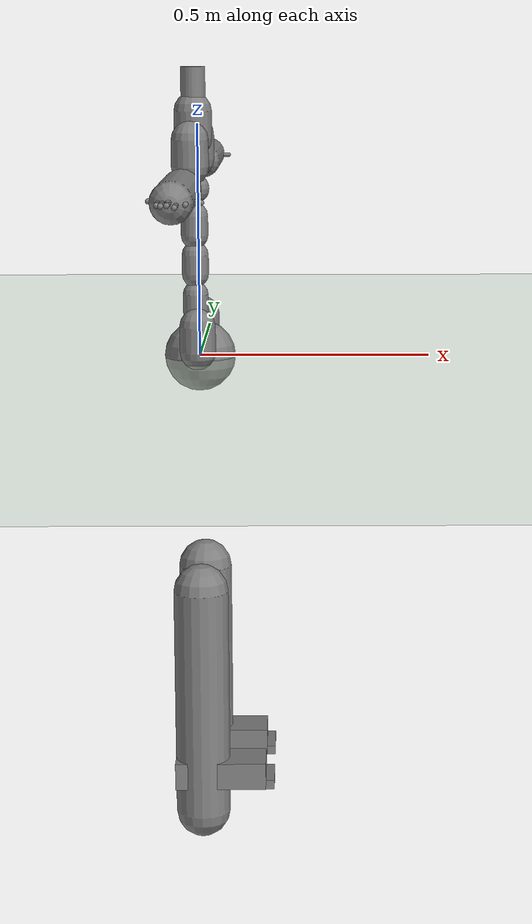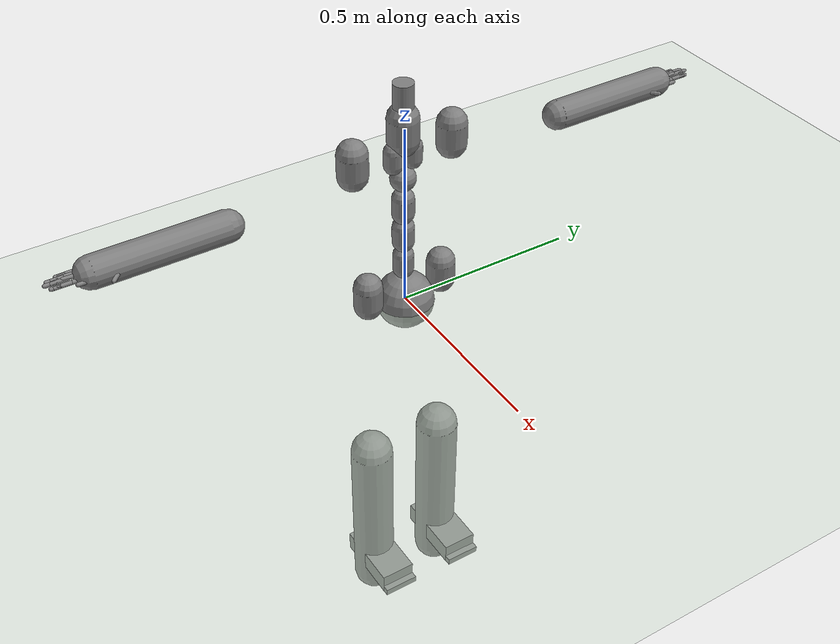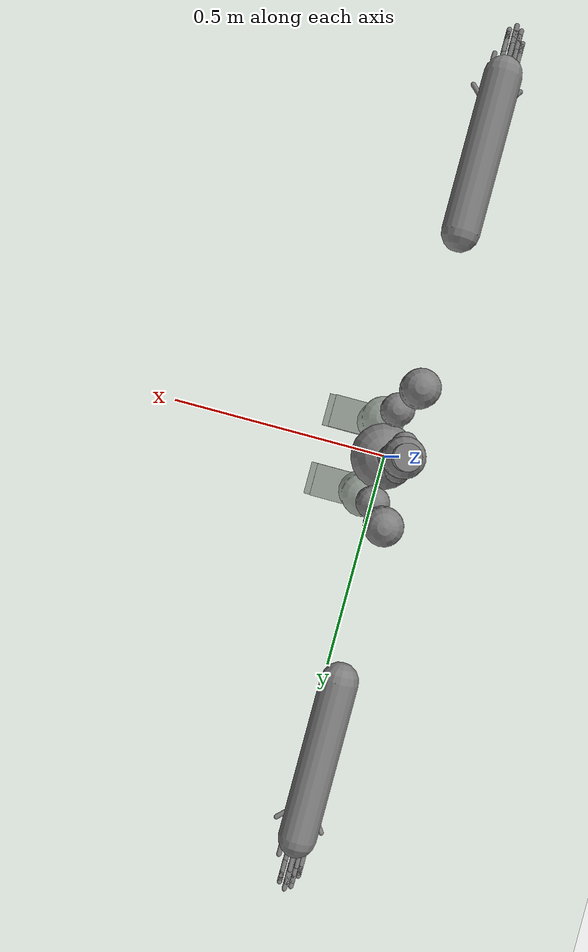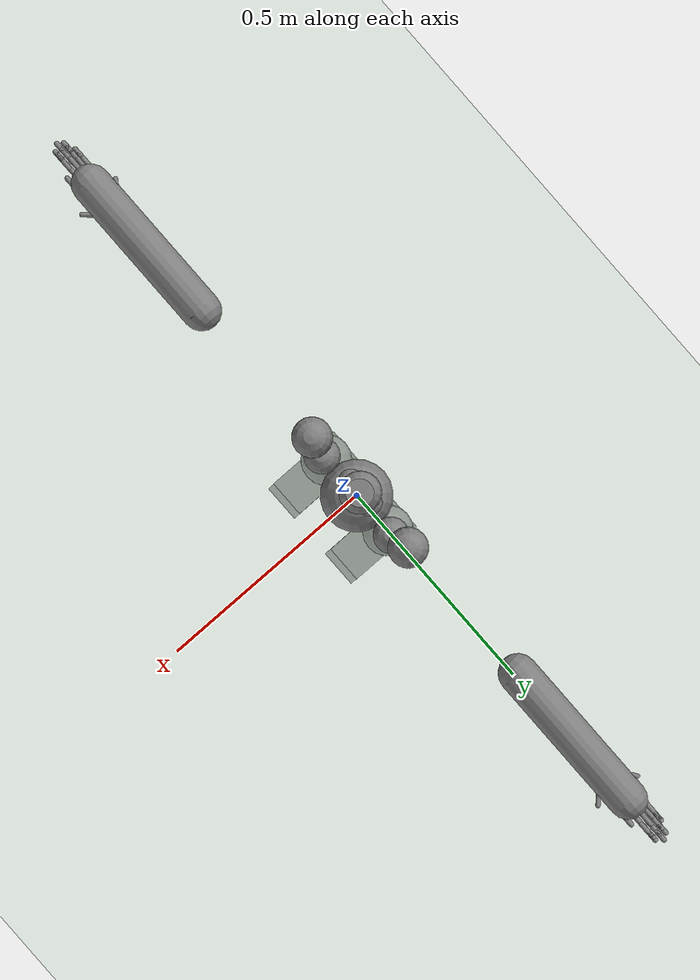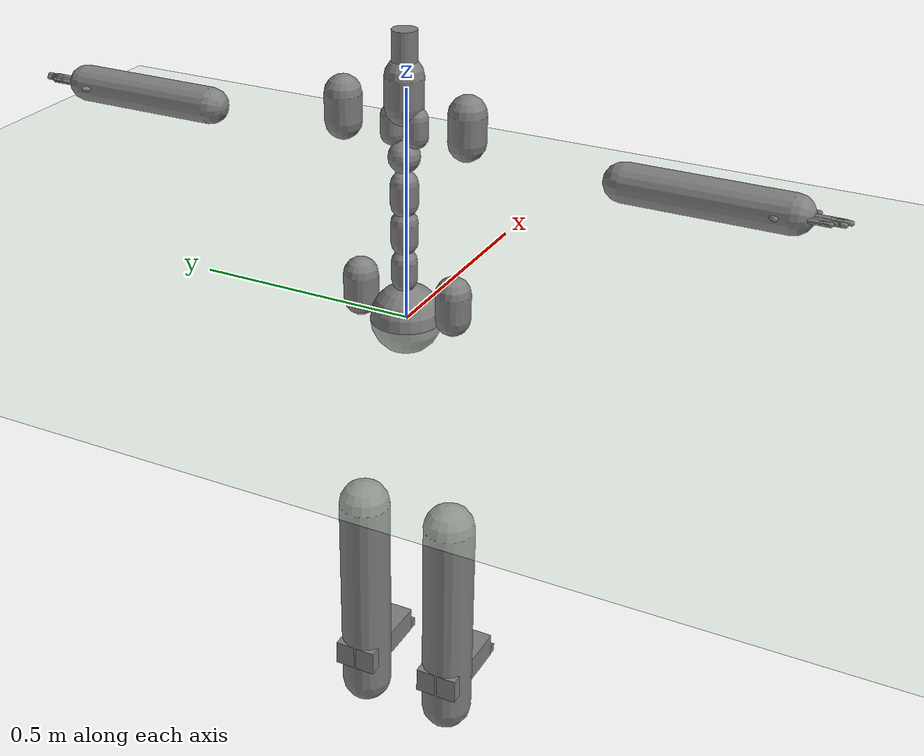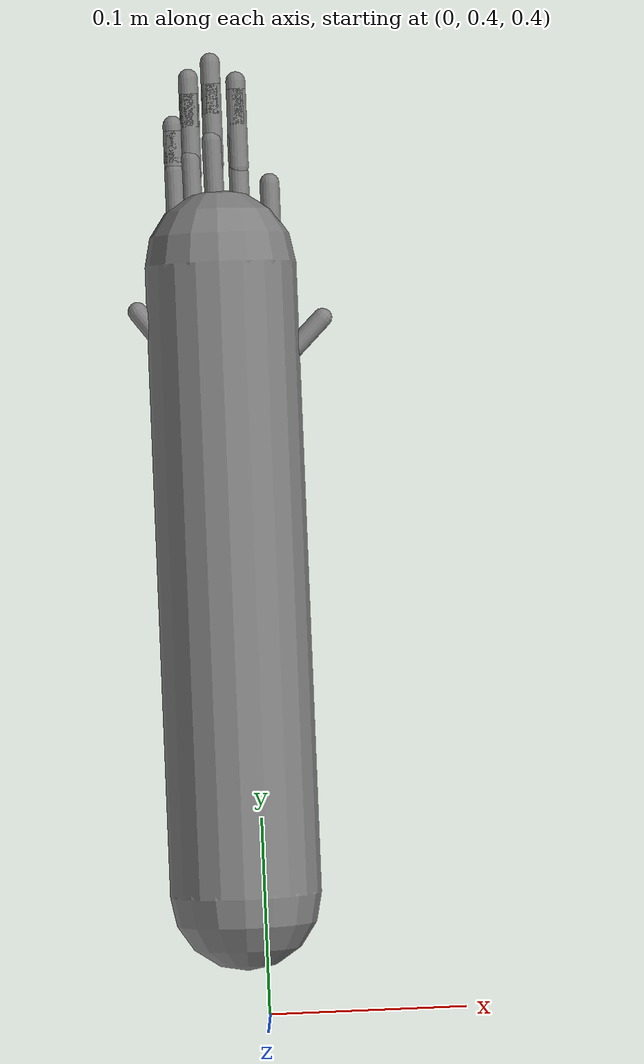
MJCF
<?xml version="1.0" ?>
<mujoco model="humanoid">
  <compiler coordinate="local"/>
  <statistic extent="2" center="0 0 1"/>
  <option timestep="0.00555"/>
  <default>
    <motor ctrlrange="-1 1" ctrllimited="true"/>
    <geom type="capsule" condim="1" friction="1.0 0.05 0.05" solimp=".9 .99 .003" solref=".015 1"/>
    <joint type="hinge" damping="0.1" stiffness="5" armature=".007" limited="true" solimplimit="0 .99 .01"/>
    <site size=".04" group="3"/>
  </default>
  <asset>
    <texture type="skybox" builtin="gradient" rgb1=".4 .5 .6" rgb2="0 0 0" width="100" height="100"/>
    <texture builtin="flat" height="1278" mark="cross" markrgb="1 1 1" name="texgeom" random="0.01" rgb1="0.8 0.6 0.4" rgb2="0.8 0.6 0.4" type="cube" width="127"/>
    <texture builtin="checker" height="100" name="texplane" rgb1="0 0 0" rgb2="0.8 0.8 0.8" type="2d" width="100"/>
    <material name="MatPlane" reflectance="0.5" shininess="1" specular="1" texrepeat="60 60" texture="texplane"/>
    <material name="geom" texture="texgeom" texuniform="true"/>
  </asset>
  <worldbody>
    <light cutoff="100" diffuse="1 1 1" dir="-0 0 -1.3" directional="true" exponent="1" pos="0 0 1.3" specular=".1 .1 .1"/>
    <geom conaffinity="1" condim="3" name="floor" pos="0 0 0" rgba="0.8 0.9 0.8 1" size="100 100 .2" type="plane" material="MatPlane"/>
    <body name="pHipOrigin" pos="0 0 0">
      <freejoint name="pHipOrigin"/>
      <geom type="sphere" contype="1" conaffinity="1" density="4629.6296296296305" size="0.07729" pos="0.0000 0.0000 -0.0000"/>
      <body name="jL5S1" pos="-0.00870986 0 0.07838852">
        <geom type="capsule" contype="1" conaffinity="1" density="1000" fromto="0 0 0.01577 0 0 0.05521" size="0.02760"/>
        <joint name="jL5S1_x" type="hinge" pos="0 0 0" axis="1 0 0" stiffness="500" damping="500" armature="0.02" range="-180.0000 180.0000"/>
        <joint name="jL5S1_y" type="hinge" pos="0 0 0" axis="0 1 0" stiffness="500" damping="500" armature="0.02" range="-180.0000 180.0000"/>
        <joint name="jL5S1_z" type="hinge" pos="0 0 0" axis="0 0 1" stiffness="500" damping="500" armature="0.02" range="-180.0000 180.0000"/>
        <body name="jL4L3" pos="0 0 0.08276130">
          <geom type="capsule" contype="1" conaffinity="1" density="1000" fromto="0 0 0.01655 0 0 0.05793" size="0.02897"/>
          <joint name="jL4L3_x" type="hinge" pos="0 0 0" axis="1 0 0" stiffness="500" damping="500" armature="0.02" range="-180.0000 180.0000"/>
          <joint name="jL4L3_y" type="hinge" pos="0 0 0" axis="0 1 0" stiffness="500" damping="500" armature="0.02" range="-180.0000 180.0000"/>
          <joint name="jL4L3_z" type="hinge" pos="0 0 0" axis="0 0 1" stiffness="500" damping="500" armature="0.02" range="-180.0000 180.0000"/>
          <body name="jL1T12" pos="-0.00064562 0 0.08368396">
            <geom type="capsule" contype="1" conaffinity="1" density="1000" fromto="0 0 0.01674 0 0 0.05858" size="0.02929"/>
            <joint name="jL1T12_x" type="hinge" pos="0 0 0" axis="1 0 0" stiffness="500" damping="500" armature="0.02" range="-180.0000 180.0000"/>
            <joint name="jL1T12_y" type="hinge" pos="0 0 0" axis="0 1 0" stiffness="500" damping="500" armature="0.02" range="-180.0000 180.0000"/>
            <joint name="jL1T12_z" type="hinge" pos="0 0 0" axis="0 0 1" stiffness="500" damping="500" armature="0.02" range="-180.0000 180.0000"/>
            <body name="jT9T8" pos="-0.00064696 0 0.08369474">
              <geom type="sphere" contype="1" conaffinity="1" density="1000" size="0.03348" pos="0.000 0.0000 0.033479"/>
              <joint name="jT9T8_x" type="hinge" pos="0 0 0" axis="1 0 0" stiffness="500" damping="500" armature="0.02" range="-180.0000 180.0000"/>
              <joint name="jT9T8_y" type="hinge" pos="0 0 0" axis="0 1 0" stiffness="500" damping="500" armature="0.02" range="-180.0000 180.0000"/>
              <joint name="jT9T8_z" type="hinge" pos="0 0 0" axis="0 0 1" stiffness="500" damping="500" armature="0.02" range="-180.0000 180.0000"/>
              <body name="jT1C7" pos="0 0 0.11634099">
                <geom type="capsule" contype="1" conaffinity="1" density="1000" fromto="0 0 0.02327 0 0 0.08144" size="0.04072"/>
                <joint name="jT1C7_x" type="hinge" pos="0 0 0" axis="1 0 0" stiffness="500" damping="500" armature="0.02" range="-180.0000 180.0000"/>
                <joint name="jT1C7_y" type="hinge" pos="0 0 0" axis="0 1 0" stiffness="500" damping="500" armature="0.02" range="-180.0000 180.0000"/>
                <joint name="jT1C7_z" type="hinge" pos="0 0 0" axis="0 0 1" stiffness="500" damping="500" armature="0.02" range="-180.0000 180.0000"/>
                <body name="jC1Head" pos="0.00103240 0 0.08750932">
                  <geom type="cylinder" contype="1" conaffinity="1" density="1000" fromto="0 0 0 0 0 0.08752" size="0.02625"/>
                  <joint name="jC1Head_x" type="hinge" pos="0 0 0" axis="1 0 0" stiffness="500" damping="500" armature="0.02" range="-180.0000 180.0000"/>
                  <joint name="jC1Head_y" type="hinge" pos="0 0 0" axis="0 1 0" stiffness="500" damping="500" armature="0.02" range="-180.0000 180.0000"/>
                  <joint name="jC1Head_z" type="hinge" pos="0 0 0" axis="0 0 1" stiffness="500" damping="500" armature="0.02" range="-180.0000 180.0000"/>
                </body>
              </body>
              <body name="jRightT4Shoulder" pos="0 -0.02693906 0.06568334">
                <geom type="capsule" contype="1" conaffinity="1" density="1000" fromto="0 0 0.01420 0 0 0.04970" size="0.02485"/>
                <joint name="jRightT4Shoulder_x" type="hinge" pos="0 0 0" axis="1 0 0" stiffness="500" damping="500" armature="0.02" range="-180.0000 180.0000"/>
                <joint name="jRightT4Shoulder_y" type="hinge" pos="0 0 0" axis="0 1 0" stiffness="500" damping="500" armature="0.02" range="-180.0000 180.0000"/>
                <joint name="jRightT4Shoulder_z" type="hinge" pos="0 0 0" axis="0 0 1" stiffness="500" damping="500" armature="0.02" range="-180.0000 180.0000"/>
                <body name="jRightShoulder" pos="0 -0.11150376 0">
                  <geom type="capsule" contype="1" conaffinity="1" density="1000" fromto="0 0 0.02230 0 0 0.07805" size="0.03903"/>
                  <joint name="jRightShoulder_x" type="hinge" pos="0 0 0" axis="1 0 0" stiffness="500" damping="500" armature="0.02" range="-180.0000 180.0000"/>
                  <joint name="jRightShoulder_y" type="hinge" pos="0 0 0" axis="0 1 0" stiffness="500" damping="500" armature="0.02" range="-180.0000 180.0000"/>
                  <joint name="jRightShoulder_z" type="hinge" pos="0 0 0" axis="0 0 1" stiffness="500" damping="500" armature="0.02" range="-180.0000 180.0000"/>
                  <body name="jRightElbow" pos="0 -0.32442185 0">
                    <geom type="capsule" contype="1" conaffinity="1" density="1000" fromto="0 0 0 0.00000000 -0.32442185 0.00000000" size="0.03893"/>
                    <joint name="jRightElbow_x" type="hinge" pos="0 0 0" axis="1 0 0" stiffness="500" damping="500" armature="0.02" range="-180.0000 180.0000"/>
                    <joint name="jRightElbow_y" type="hinge" pos="0 0 0" axis="0 1 0" stiffness="500" damping="500" armature="0.02" range="-180.0000 180.0000"/>
                    <joint name="jRightElbow_z" type="hinge" pos="0 0 0" axis="0 0 1" stiffness="500" damping="500" armature="0.02" range="-180.0000 180.0000"/>
                    <body name="jRightWrist" pos="0.00009744 -0.24210083 0">
                      <geom density="1000" type="box" pos="0 0 0" size="0.035 0.03 0.01" quat="1.0000 0.0000 0.0000 0.0000"/>
                      <joint name="jRightWrist_x" type="hinge" pos="0 0 0" axis="1 0 0" stiffness="500" damping="500" armature="0.02" range="-180.0000 180.0000"/>
                      <joint name="jRightWrist_y" type="hinge" pos="0 0 0" axis="0 1 0" stiffness="500" damping="500" armature="0.02" range="-180.0000 180.0000"/>
                      <joint name="jRightWrist_z" type="hinge" pos="0 0 0" axis="0 0 1" stiffness="500" damping="500" armature="0.02" range="-180.0000 180.0000"/>
                      <body name="jRightFirstCMC" pos="0.02600324 -0.02492556 -0.00117759">
                        <geom type="capsule" contype="1" conaffinity="1" density="1000" fromto="0 0 0 0.02600324 -0.02492556 -0.00117759" size="0.005"/>
                        <joint name="jRightFirstCMC_x" type="hinge" pos="0 0 0" axis="1 0 0" stiffness="500" damping="500" armature="0.02" range="-180.0000 180.0000"/>
                        <joint name="jRightFirstCMC_y" type="hinge" pos="0 0 0" axis="0 1 0" stiffness="500" damping="500" armature="0.02" range="-180.0000 180.0000"/>
                        <joint name="jRightFirstCMC_z" type="hinge" pos="0 0 0" axis="0 0 1" stiffness="500" damping="500" armature="0.02" range="-180.0000 180.0000"/>
                        <body name="jRightFirstMCP" pos="0.00122664 -0.03461487 0.00073141">
                          <geom type="capsule" contype="1" conaffinity="1" density="1000" fromto="0 0 0 0.00122664 -0.03461487 0.00073141" size="0.005"/>
                          <joint name="jRightFirstMCP_x" type="hinge" pos="0 0 0" axis="1 0 0" stiffness="500" damping="500" armature="0.02" range="-180.0000 180.0000"/>
                          <joint name="jRightFirstMCP_y" type="hinge" pos="0 0 0" axis="0 1 0" stiffness="500" damping="500" armature="0.02" range="-180.0000 180.0000"/>
                          <joint name="jRightFirstMCP_z" type="hinge" pos="0 0 0" axis="0 0 1" stiffness="500" damping="500" armature="0.02" range="-180.0000 180.0000"/>
                          <body name="jRightIP" pos="0 -0.03040452 0">
                            <geom type="capsule" contype="1" conaffinity="1" density="1000" fromto="0 0 0 0.00000000 -0.03040452 0.00000000" size="0.005"/>
                            <joint name="jRightIP_x" type="hinge" pos="0 0 0" axis="1 0 0" stiffness="500" damping="500" armature="0.02" range="-180.0000 180.0000"/>
                            <joint name="jRightIP_y" type="hinge" pos="0 0 0" axis="0 1 0" stiffness="500" damping="500" armature="0.02" range="-180.0000 180.0000"/>
                            <joint name="jRightIP_z" type="hinge" pos="0 0 0" axis="0 0 1" stiffness="500" damping="500" armature="0.02" range="-180.0000 180.0000"/>
                          </body>
                        </body>
                      </body>
                      <body name="jRightSecondCMC" pos="0.01150675 -0.03361907 -0.00058640">
                        <geom type="capsule" contype="1" conaffinity="1" density="1000" fromto="0 0 0 0.01150675 -0.03361907 -0.00058640" size="0.005"/>
                        <joint name="jRightSecondCMC_x" type="hinge" pos="0 0 0" axis="1 0 0" stiffness="500" damping="500" armature="0.02" range="-180.0000 180.0000"/>
                        <joint name="jRightSecondCMC_y" type="hinge" pos="0 0 0" axis="0 1 0" stiffness="500" damping="500" armature="0.02" range="-180.0000 180.0000"/>
                        <joint name="jRightSecondCMC_z" type="hinge" pos="0 0 0" axis="0 0 1" stiffness="500" damping="500" armature="0.02" range="-180.0000 180.0000"/>
                        <body name="jRightSecondMCP" pos="-0.00035076 -0.05594368 -0.00058032">
                          <geom type="capsule" contype="1" conaffinity="1" density="1000" fromto="0 0 0 -0.00035076 -0.05594368 -0.00058032" size="0.005"/>
                          <joint name="jRightSecondMCP_x" type="hinge" pos="0 0 0" axis="1 0 0" stiffness="500" damping="500" armature="0.02" range="-180.0000 180.0000"/>
                          <joint name="jRightSecondMCP_y" type="hinge" pos="0 0 0" axis="0 1 0" stiffness="500" damping="500" armature="0.02" range="-180.0000 180.0000"/>
                          <joint name="jRightSecondMCP_z" type="hinge" pos="0 0 0" axis="0 0 1" stiffness="500" damping="500" armature="0.02" range="-180.0000 180.0000"/>
                          <body name="jRightSecondPIP" pos="0 -0.04001878 0">
                            <geom type="capsule" contype="1" conaffinity="1" density="1000" fromto="0 0 0 0.00000000 -0.04001878 0.00000000" size="0.005"/>
                            <joint name="jRightSecondPIP_x" type="hinge" pos="0 0 0" axis="1 0 0" stiffness="500" damping="500" armature="0.02" range="-180.0000 180.0000"/>
                            <joint name="jRightSecondPIP_y" type="hinge" pos="0 0 0" axis="0 1 0" stiffness="500" damping="500" armature="0.02" range="-180.0000 180.0000"/>
                            <joint name="jRightSecondPIP_z" type="hinge" pos="0 0 0" axis="0 0 1" stiffness="500" damping="500" armature="0.02" range="-180.0000 180.0000"/>
                            <body name="jRightSecondDIP" pos="0 -0.02210844 0">
                              <geom type="capsule" contype="1" conaffinity="1" density="1000" fromto="0 0 0 0.00000000 -0.02210844 0.00000000" size="0.005"/>
                              <joint name="jRightSecondDIP_x" type="hinge" pos="0 0 0" axis="1 0 0" stiffness="500" damping="500" armature="0.02" range="-180.0000 180.0000"/>
                              <joint name="jRightSecondDIP_y" type="hinge" pos="0 0 0" axis="0 1 0" stiffness="500" damping="500" armature="0.02" range="-180.0000 180.0000"/>
                              <joint name="jRightSecondDIP_z" type="hinge" pos="0 0 0" axis="0 0 1" stiffness="500" damping="500" armature="0.02" range="-180.0000 180.0000"/>
                            </body>
                          </body>
                        </body>
                      </body>
                      <body name="jRightThirdCMC" pos="-0.00065361 -0.03534583 0.00148599">
                        <geom type="capsule" contype="1" conaffinity="1" density="1000" fromto="0 0 0 -0.00065361 -0.03534583 0.00148599" size="0.005"/>
                        <joint name="jRightThirdCMC_x" type="hinge" pos="0 0 0" axis="1 0 0" stiffness="500" damping="500" armature="0.02" range="-180.0000 180.0000"/>
                        <joint name="jRightThirdCMC_y" type="hinge" pos="0 0 0" axis="0 1 0" stiffness="500" damping="500" armature="0.02" range="-180.0000 180.0000"/>
                        <joint name="jRightThirdCMC_z" type="hinge" pos="0 0 0" axis="0 0 1" stiffness="500" damping="500" armature="0.02" range="-180.0000 180.0000"/>
                        <body name="jRightThirdMCP" pos="-0.00065409 -0.05419156 0.00147434">
                          <geom type="capsule" contype="1" conaffinity="1" density="1000" fromto="0 0 0 -0.00065409 -0.05419156 0.00147434" size="0.005"/>
                          <joint name="jRightThirdMCP_x" type="hinge" pos="0 0 0" axis="1 0 0" stiffness="500" damping="500" armature="0.02" range="-180.0000 180.0000"/>
                          <joint name="jRightThirdMCP_y" type="hinge" pos="0 0 0" axis="0 1 0" stiffness="500" damping="500" armature="0.02" range="-180.0000 180.0000"/>
                          <joint name="jRightThirdMCP_z" type="hinge" pos="0 0 0" axis="0 0 1" stiffness="500" damping="500" armature="0.02" range="-180.0000 180.0000"/>
                          <body name="jRightThirdPIP" pos="0 -0.04138725 0">
                            <geom type="capsule" contype="1" conaffinity="1" density="1000" fromto="0 0 0 0.00000000 -0.04138725 0.00000000" size="0.005"/>
                            <joint name="jRightThirdPIP_x" type="hinge" pos="0 0 0" axis="1 0 0" stiffness="500" damping="500" armature="0.02" range="-180.0000 180.0000"/>
                            <joint name="jRightThirdPIP_y" type="hinge" pos="0 0 0" axis="0 1 0" stiffness="500" damping="500" armature="0.02" range="-180.0000 180.0000"/>
                            <joint name="jRightThirdPIP_z" type="hinge" pos="0 0 0" axis="0 0 1" stiffness="500" damping="500" armature="0.02" range="-180.0000 180.0000"/>
                            <body name="jRightThirdDIP" pos="0 -0.02623139 0">
                              <geom type="capsule" contype="1" conaffinity="1" density="1000" fromto="0 0 0 0.00000000 -0.02623139 0.00000000" size="0.005"/>
                              <joint name="jRightThirdDIP_x" type="hinge" pos="0 0 0" axis="1 0 0" stiffness="500" damping="500" armature="0.02" range="-180.0000 180.0000"/>
                              <joint name="jRightThirdDIP_y" type="hinge" pos="0 0 0" axis="0 1 0" stiffness="500" damping="500" armature="0.02" range="-180.0000 180.0000"/>
                              <joint name="jRightThirdDIP_z" type="hinge" pos="0 0 0" axis="0 0 1" stiffness="500" damping="500" armature="0.02" range="-180.0000 180.0000"/>
                            </body>
                          </body>
                        </body>
                      </body>
                      <body name="jRightFourthCMC" pos="-0.01198094 -0.03336889 0.00078545">
                        <geom type="capsule" contype="1" conaffinity="1" density="1000" fromto="0 0 0 -0.01198094 -0.03336889 0.00078545" size="0.005"/>
                        <joint name="jRightFourthCMC_x" type="hinge" pos="0 0 0" axis="1 0 0" stiffness="500" damping="500" armature="0.02" range="-180.0000 180.0000"/>
                        <joint name="jRightFourthCMC_y" type="hinge" pos="0 0 0" axis="0 1 0" stiffness="500" damping="500" armature="0.02" range="-180.0000 180.0000"/>
                        <joint name="jRightFourthCMC_z" type="hinge" pos="0 0 0" axis="0 0 1" stiffness="500" damping="500" armature="0.02" range="-180.0000 180.0000"/>
                        <body name="jRightFourthMCP" pos="-0.00037092 -0.05083819 0.00079871">
                          <geom type="capsule" contype="1" conaffinity="1" density="1000" fromto="0 0 0 -0.00037092 -0.05083819 0.00079871" size="0.005"/>
                          <joint name="jRightFourthMCP_x" type="hinge" pos="0 0 0" axis="1 0 0" stiffness="500" damping="500" armature="0.02" range="-180.0000 180.0000"/>
                          <joint name="jRightFourthMCP_y" type="hinge" pos="0 0 0" axis="0 1 0" stiffness="500" damping="500" armature="0.02" range="-180.0000 180.0000"/>
                          <joint name="jRightFourthMCP_z" type="hinge" pos="0 0 0" axis="0 0 1" stiffness="500" damping="500" armature="0.02" range="-180.0000 180.0000"/>
                          <body name="jRightFourthPIP" pos="0 -0.04179491 0">
                            <geom type="capsule" contype="1" conaffinity="1" density="1000" fromto="0 0 0 0.00000000 -0.04179491 0.00000000" size="0.005"/>
                            <joint name="jRightFourthPIP_x" type="hinge" pos="0 0 0" axis="1 0 0" stiffness="500" damping="500" armature="0.02" range="-180.0000 180.0000"/>
                            <joint name="jRightFourthPIP_y" type="hinge" pos="0 0 0" axis="0 1 0" stiffness="500" damping="500" armature="0.02" range="-180.0000 180.0000"/>
                            <joint name="jRightFourthPIP_z" type="hinge" pos="0 0 0" axis="0 0 1" stiffness="500" damping="500" armature="0.02" range="-180.0000 180.0000"/>
                            <body name="jRightFourthDIP" pos="0 -0.02495660 0">
                              <geom type="capsule" contype="1" conaffinity="1" density="1000" fromto="0 0 0 0.00000000 -0.02495660 0.00000000" size="0.005"/>
                              <joint name="jRightFourthDIP_x" type="hinge" pos="0 0 0" axis="1 0 0" stiffness="500" damping="500" armature="0.02" range="-180.0000 180.0000"/>
                              <joint name="jRightFourthDIP_y" type="hinge" pos="0 0 0" axis="0 1 0" stiffness="500" damping="500" armature="0.02" range="-180.0000 180.0000"/>
                              <joint name="jRightFourthDIP_z" type="hinge" pos="0 0 0" axis="0 0 1" stiffness="500" damping="500" armature="0.02" range="-180.0000 180.0000"/>
                            </body>
                          </body>
                        </body>
                      </body>
                      <body name="jRightFifthCMC" pos="-0.02103018 -0.02930316 0.00057806">
                        <geom type="capsule" contype="1" conaffinity="1" density="1000" fromto="0 0 0 -0.02103018 -0.02930316 0.00057806" size="0.005"/>
                        <joint name="jRightFifthCMC_x" type="hinge" pos="0 0 0" axis="1 0 0" stiffness="500" damping="500" armature="0.02" range="-180.0000 180.0000"/>
                        <joint name="jRightFifthCMC_y" type="hinge" pos="0 0 0" axis="0 1 0" stiffness="500" damping="500" armature="0.02" range="-180.0000 180.0000"/>
                        <joint name="jRightFifthCMC_z" type="hinge" pos="0 0 0" axis="0 0 1" stiffness="500" damping="500" armature="0.02" range="-180.0000 180.0000"/>
                        <body name="jRightFifthMCP" pos="-0.00000739 -0.05004550 0.00068869">
                          <geom type="capsule" contype="1" conaffinity="1" density="1000" fromto="0 0 0 -0.00000739 -0.05004550 0.00068869" size="0.005"/>
                          <joint name="jRightFifthMCP_x" type="hinge" pos="0 0 0" axis="1 0 0" stiffness="500" damping="500" armature="0.02" range="-180.0000 180.0000"/>
                          <joint name="jRightFifthMCP_y" type="hinge" pos="0 0 0" axis="0 1 0" stiffness="500" damping="500" armature="0.02" range="-180.0000 180.0000"/>
                          <joint name="jRightFifthMCP_z" type="hinge" pos="0 0 0" axis="0 0 1" stiffness="500" damping="500" armature="0.02" range="-180.0000 180.0000"/>
                          <body name="jRightFifthPIP" pos="0 -0.03512114 0">
                            <geom type="capsule" contype="1" conaffinity="1" density="1000" fromto="0 0 0 0.00000000 -0.03512114 0.00000000" size="0.005"/>
                            <joint name="jRightFifthPIP_x" type="hinge" pos="0 0 0" axis="1 0 0" stiffness="500" damping="500" armature="0.02" range="-180.0000 180.0000"/>
                            <joint name="jRightFifthPIP_y" type="hinge" pos="0 0 0" axis="0 1 0" stiffness="500" damping="500" armature="0.02" range="-180.0000 180.0000"/>
                            <joint name="jRightFifthPIP_z" type="hinge" pos="0 0 0" axis="0 0 1" stiffness="500" damping="500" armature="0.02" range="-180.0000 180.0000"/>
                            <body name="jRightFifthDIP" pos="0 -0.01907884 0">
                              <geom type="capsule" contype="1" conaffinity="1" density="1000" fromto="0 0 0 0.00000000 -0.01907884 0.00000000" size="0.005"/>
                              <joint name="jRightFifthDIP_x" type="hinge" pos="0 0 0" axis="1 0 0" stiffness="500" damping="500" armature="0.02" range="-180.0000 180.0000"/>
                              <joint name="jRightFifthDIP_y" type="hinge" pos="0 0 0" axis="0 1 0" stiffness="500" damping="500" armature="0.02" range="-180.0000 180.0000"/>
                              <joint name="jRightFifthDIP_z" type="hinge" pos="0 0 0" axis="0 0 1" stiffness="500" damping="500" armature="0.02" range="-180.0000 180.0000"/>
                            </body>
                          </body>
                        </body>
                      </body>
                    </body>
                  </body>
                </body>
              </body>
              <body name="jLeftT4Shoulder" pos="0 0.02686830 0.06551082">
                <geom type="capsule" contype="1" conaffinity="1" density="1000" fromto="0 0 0.01416 0 0 0.04956" size="0.02478"/>
                <joint name="jLeftT4Shoulder_x" type="hinge" pos="0 0 0" axis="1 0 0" stiffness="500" damping="500" armature="0.02" range="-180.0000 180.0000"/>
                <joint name="jLeftT4Shoulder_y" type="hinge" pos="0 0 0" axis="0 1 0" stiffness="500" damping="500" armature="0.02" range="-180.0000 180.0000"/>
                <joint name="jLeftT4Shoulder_z" type="hinge" pos="0 0 0" axis="0 0 1" stiffness="500" damping="500" armature="0.02" range="-180.0000 180.0000"/>
                <body name="jLeftShoulder" pos="0 0.11139681 0">
                  <geom type="capsule" contype="1" conaffinity="1" density="1000" fromto="0 0 0.02228 0 0 0.07798" size="0.03899"/>
                  <joint name="jLeftShoulder_x" type="hinge" pos="0 0 0" axis="1 0 0" stiffness="500" damping="500" armature="0.02" range="-180.0000 180.0000"/>
                  <joint name="jLeftShoulder_y" type="hinge" pos="0 0 0" axis="0 1 0" stiffness="500" damping="500" armature="0.02" range="-180.0000 180.0000"/>
                  <joint name="jLeftShoulder_z" type="hinge" pos="0 0 0" axis="0 0 1" stiffness="500" damping="500" armature="0.02" range="-180.0000 180.0000"/>
                  <body name="jLeftElbow" pos="0 0.32252035 0">
                    <geom type="capsule" contype="1" conaffinity="1" density="1000" fromto="0 0 0 0.00000000 0.32252035 0.00000000" size="0.03870"/>
                    <joint name="jLeftElbow_x" type="hinge" pos="0 0 0" axis="1 0 0" stiffness="500" damping="500" armature="0.02" range="-180.0000 180.0000"/>
                    <joint name="jLeftElbow_y" type="hinge" pos="0 0 0" axis="0 1 0" stiffness="500" damping="500" armature="0.02" range="-180.0000 180.0000"/>
                    <joint name="jLeftElbow_z" type="hinge" pos="0 0 0" axis="0 0 1" stiffness="500" damping="500" armature="0.02" range="-180.0000 180.0000"/>
                    <body name="jLeftWrist" pos="0.00009760 0.24250106 0">
                      <geom density="1000" type="box" pos="0 0 0" size="0.035 0.03 0.01" quat="1.0000 0.0000 0.0000 0.0000"/>
                      <joint name="jLeftWrist_x" type="hinge" pos="0 0 0" axis="1 0 0" stiffness="500" damping="500" armature="0.02" range="-180.0000 180.0000"/>
                      <joint name="jLeftWrist_y" type="hinge" pos="0 0 0" axis="0 1 0" stiffness="500" damping="500" armature="0.02" range="-180.0000 180.0000"/>
                      <joint name="jLeftWrist_z" type="hinge" pos="0 0 0" axis="0 0 1" stiffness="500" damping="500" armature="0.02" range="-180.0000 180.0000"/>
                      <body name="jLeftFirstCMC" pos="0.02545104 0.02551115 -0.00113910">
                        <geom type="capsule" contype="1" conaffinity="1" density="1000" fromto="0 0 0 0.02545104 0.02551115 -0.00113910" size="0.005"/>
                        <joint name="jLeftFirstCMC_x" type="hinge" pos="0 0 0" axis="1 0 0" stiffness="500" damping="500" armature="0.02" range="-180.0000 180.0000"/>
                        <joint name="jLeftFirstCMC_y" type="hinge" pos="0 0 0" axis="0 1 0" stiffness="500" damping="500" armature="0.02" range="-180.0000 180.0000"/>
                        <joint name="jLeftFirstCMC_z" type="hinge" pos="0 0 0" axis="0 0 1" stiffness="500" damping="500" armature="0.02" range="-180.0000 180.0000"/>
                        <body name="jLeftFirstMCP" pos="0.00121482 0.03461409 0.00071279">
                          <geom type="capsule" contype="1" conaffinity="1" density="1000" fromto="0 0 0 0.00121482 0.03461409 0.00071279" size="0.005"/>
                          <joint name="jLeftFirstMCP_x" type="hinge" pos="0 0 0" axis="1 0 0" stiffness="500" damping="500" armature="0.02" range="-180.0000 180.0000"/>
                          <joint name="jLeftFirstMCP_y" type="hinge" pos="0 0 0" axis="0 1 0" stiffness="500" damping="500" armature="0.02" range="-180.0000 180.0000"/>
                          <joint name="jLeftFirstMCP_z" type="hinge" pos="0 0 0" axis="0 0 1" stiffness="500" damping="500" armature="0.02" range="-180.0000 180.0000"/>
                          <body name="jLeftIP" pos="0 0.03040452 0">
                            <geom type="capsule" contype="1" conaffinity="1" density="1000" fromto="0 0 0 0.00000000 0.03040452 0.00000000" size="0.005"/>
                            <joint name="jLeftIP_x" type="hinge" pos="0 0 0" axis="1 0 0" stiffness="500" damping="500" armature="0.02" range="-180.0000 180.0000"/>
                            <joint name="jLeftIP_y" type="hinge" pos="0 0 0" axis="0 1 0" stiffness="500" damping="500" armature="0.02" range="-180.0000 180.0000"/>
                            <joint name="jLeftIP_z" type="hinge" pos="0 0 0" axis="0 0 1" stiffness="500" damping="500" armature="0.02" range="-180.0000 180.0000"/>
                          </body>
                        </body>
                      </body>
                      <body name="jLeftSecondCMC" pos="0.01163928 0.03355721 -0.00059124">
                        <geom type="capsule" contype="1" conaffinity="1" density="1000" fromto="0 0 0 0.01163928 0.03355721 -0.00059124" size="0.005"/>
                        <joint name="jLeftSecondCMC_x" type="hinge" pos="0 0 0" axis="1 0 0" stiffness="500" damping="500" armature="0.02" range="-180.0000 180.0000"/>
                        <joint name="jLeftSecondCMC_y" type="hinge" pos="0 0 0" axis="0 1 0" stiffness="500" damping="500" armature="0.02" range="-180.0000 180.0000"/>
                        <joint name="jLeftSecondCMC_z" type="hinge" pos="0 0 0" axis="0 0 1" stiffness="500" damping="500" armature="0.02" range="-180.0000 180.0000"/>
                        <body name="jLeftSecondMCP" pos="-0.00030584 0.05594482 -0.00058749">
                          <geom type="capsule" contype="1" conaffinity="1" density="1000" fromto="0 0 0 -0.00030584 0.05594482 -0.00058749" size="0.005"/>
                          <joint name="jLeftSecondMCP_x" type="hinge" pos="0 0 0" axis="1 0 0" stiffness="500" damping="500" armature="0.02" range="-180.0000 180.0000"/>
                          <joint name="jLeftSecondMCP_y" type="hinge" pos="0 0 0" axis="0 1 0" stiffness="500" damping="500" armature="0.02" range="-180.0000 180.0000"/>
                          <joint name="jLeftSecondMCP_z" type="hinge" pos="0 0 0" axis="0 0 1" stiffness="500" damping="500" armature="0.02" range="-180.0000 180.0000"/>
                          <body name="jLeftSecondPIP" pos="0 0.04001878 0">
                            <geom type="capsule" contype="1" conaffinity="1" density="1000" fromto="0 0 0 0.00000000 0.04001878 0.00000000" size="0.005"/>
                            <joint name="jLeftSecondPIP_x" type="hinge" pos="0 0 0" axis="1 0 0" stiffness="500" damping="500" armature="0.02" range="-180.0000 180.0000"/>
                            <joint name="jLeftSecondPIP_y" type="hinge" pos="0 0 0" axis="0 1 0" stiffness="500" damping="500" armature="0.02" range="-180.0000 180.0000"/>
                            <joint name="jLeftSecondPIP_z" type="hinge" pos="0 0 0" axis="0 0 1" stiffness="500" damping="500" armature="0.02" range="-180.0000 180.0000"/>
                            <body name="jLeftSecondDIP" pos="0 0.02210844 0">
                              <geom type="capsule" contype="1" conaffinity="1" density="1000" fromto="0 0 0 0.00000000 0.02210844 0.00000000" size="0.005"/>
                              <joint name="jLeftSecondDIP_x" type="hinge" pos="0 0 0" axis="1 0 0" stiffness="500" damping="500" armature="0.02" range="-180.0000 180.0000"/>
                              <joint name="jLeftSecondDIP_y" type="hinge" pos="0 0 0" axis="0 1 0" stiffness="500" damping="500" armature="0.02" range="-180.0000 180.0000"/>
                              <joint name="jLeftSecondDIP_z" type="hinge" pos="0 0 0" axis="0 0 1" stiffness="500" damping="500" armature="0.02" range="-180.0000 180.0000"/>
                            </body>
                          </body>
                        </body>
                      </body>
                      <body name="jLeftThirdCMC" pos="-0.00065745 0.03534901 0.00143646">
                        <geom type="capsule" contype="1" conaffinity="1" density="1000" fromto="0 0 0 -0.00065745 0.03534901 0.00143646" size="0.005"/>
                        <joint name="jLeftThirdCMC_x" type="hinge" pos="0 0 0" axis="1 0 0" stiffness="500" damping="500" armature="0.02" range="-180.0000 180.0000"/>
                        <joint name="jLeftThirdCMC_y" type="hinge" pos="0 0 0" axis="0 1 0" stiffness="500" damping="500" armature="0.02" range="-180.0000 180.0000"/>
                        <joint name="jLeftThirdCMC_z" type="hinge" pos="0 0 0" axis="0 0 1" stiffness="500" damping="500" armature="0.02" range="-180.0000 180.0000"/>
                        <body name="jLeftThirdMCP" pos="-0.00065937 0.05419261 0.00144470">
                          <geom type="capsule" contype="1" conaffinity="1" density="1000" fromto="0 0 0 -0.00065937 0.05419261 0.00144470" size="0.005"/>
                          <joint name="jLeftThirdMCP_x" type="hinge" pos="0 0 0" axis="1 0 0" stiffness="500" damping="500" armature="0.02" range="-180.0000 180.0000"/>
                          <joint name="jLeftThirdMCP_y" type="hinge" pos="0 0 0" axis="0 1 0" stiffness="500" damping="500" armature="0.02" range="-180.0000 180.0000"/>
                          <joint name="jLeftThirdMCP_z" type="hinge" pos="0 0 0" axis="0 0 1" stiffness="500" damping="500" armature="0.02" range="-180.0000 180.0000"/>
                          <body name="jLeftThirdPIP" pos="0 0.04138725 0">
                            <geom type="capsule" contype="1" conaffinity="1" density="1000" fromto="0 0 0 0.00000000 0.04138725 0.00000000" size="0.005"/>
                            <joint name="jLeftThirdPIP_x" type="hinge" pos="0 0 0" axis="1 0 0" stiffness="500" damping="500" armature="0.02" range="-180.0000 180.0000"/>
                            <joint name="jLeftThirdPIP_y" type="hinge" pos="0 0 0" axis="0 1 0" stiffness="500" damping="500" armature="0.02" range="-180.0000 180.0000"/>
                            <joint name="jLeftThirdPIP_z" type="hinge" pos="0 0 0" axis="0 0 1" stiffness="500" damping="500" armature="0.02" range="-180.0000 180.0000"/>
                            <body name="jLeftThirdDIP" pos="0 0.02623139 0">
                              <geom type="capsule" contype="1" conaffinity="1" density="1000" fromto="0 0 0 0.00000000 0.02623139 0.00000000" size="0.005"/>
                              <joint name="jLeftThirdDIP_x" type="hinge" pos="0 0 0" axis="1 0 0" stiffness="500" damping="500" armature="0.02" range="-180.0000 180.0000"/>
                              <joint name="jLeftThirdDIP_y" type="hinge" pos="0 0 0" axis="0 1 0" stiffness="500" damping="500" armature="0.02" range="-180.0000 180.0000"/>
                              <joint name="jLeftThirdDIP_z" type="hinge" pos="0 0 0" axis="0 0 1" stiffness="500" damping="500" armature="0.02" range="-180.0000 180.0000"/>
                            </body>
                          </body>
                        </body>
                      </body>
                      <body name="jLeftFourthCMC" pos="-0.01242056 0.03319821 0.00083846">
                        <geom type="capsule" contype="1" conaffinity="1" density="1000" fromto="0 0 0 -0.01242056 0.03319821 0.00083846" size="0.005"/>
                        <joint name="jLeftFourthCMC_x" type="hinge" pos="0 0 0" axis="1 0 0" stiffness="500" damping="500" armature="0.02" range="-180.0000 180.0000"/>
                        <joint name="jLeftFourthCMC_y" type="hinge" pos="0 0 0" axis="0 1 0" stiffness="500" damping="500" armature="0.02" range="-180.0000 180.0000"/>
                        <joint name="jLeftFourthCMC_z" type="hinge" pos="0 0 0" axis="0 0 1" stiffness="500" damping="500" armature="0.02" range="-180.0000 180.0000"/>
                        <body name="jLeftFourthMCP" pos="-0.00039889 0.05083529 0.00084473">
                          <geom type="capsule" contype="1" conaffinity="1" density="1000" fromto="0 0 0 -0.00039889 0.05083529 0.00084473" size="0.005"/>
                          <joint name="jLeftFourthMCP_x" type="hinge" pos="0 0 0" axis="1 0 0" stiffness="500" damping="500" armature="0.02" range="-180.0000 180.0000"/>
                          <joint name="jLeftFourthMCP_y" type="hinge" pos="0 0 0" axis="0 1 0" stiffness="500" damping="500" armature="0.02" range="-180.0000 180.0000"/>
                          <joint name="jLeftFourthMCP_z" type="hinge" pos="0 0 0" axis="0 0 1" stiffness="500" damping="500" armature="0.02" range="-180.0000 180.0000"/>
                          <body name="jLeftFourthPIP" pos="0 0.04179491 0">
                            <geom type="capsule" contype="1" conaffinity="1" density="1000" fromto="0 0 0 0.00000000 0.04179491 0.00000000" size="0.005"/>
                            <joint name="jLeftFourthPIP_x" type="hinge" pos="0 0 0" axis="1 0 0" stiffness="500" damping="500" armature="0.02" range="-180.0000 180.0000"/>
                            <joint name="jLeftFourthPIP_y" type="hinge" pos="0 0 0" axis="0 1 0" stiffness="500" damping="500" armature="0.02" range="-180.0000 180.0000"/>
                            <joint name="jLeftFourthPIP_z" type="hinge" pos="0 0 0" axis="0 0 1" stiffness="500" damping="500" armature="0.02" range="-180.0000 180.0000"/>
                            <body name="jLeftFourthDIP" pos="0 0.02495660 0">
                              <geom type="capsule" contype="1" conaffinity="1" density="1000" fromto="0 0 0 0.00000000 0.02495660 0.00000000" size="0.005"/>
                              <joint name="jLeftFourthDIP_x" type="hinge" pos="0 0 0" axis="1 0 0" stiffness="500" damping="500" armature="0.02" range="-180.0000 180.0000"/>
                              <joint name="jLeftFourthDIP_y" type="hinge" pos="0 0 0" axis="0 1 0" stiffness="500" damping="500" armature="0.02" range="-180.0000 180.0000"/>
                              <joint name="jLeftFourthDIP_z" type="hinge" pos="0 0 0" axis="0 0 1" stiffness="500" damping="500" armature="0.02" range="-180.0000 180.0000"/>
                            </body>
                          </body>
                        </body>
                      </body>
                      <body name="jLeftFifthCMC" pos="-0.02166726 0.02883990 0.00058735">
                        <geom type="capsule" contype="1" conaffinity="1" density="1000" fromto="0 0 0 -0.02166726 0.02883990 0.00058735" size="0.005"/>
                        <joint name="jLeftFifthCMC_x" type="hinge" pos="0 0 0" axis="1 0 0" stiffness="500" damping="500" armature="0.02" range="-180.0000 180.0000"/>
                        <joint name="jLeftFifthCMC_y" type="hinge" pos="0 0 0" axis="0 1 0" stiffness="500" damping="500" armature="0.02" range="-180.0000 180.0000"/>
                        <joint name="jLeftFifthCMC_z" type="hinge" pos="0 0 0" axis="0 0 1" stiffness="500" damping="500" armature="0.02" range="-180.0000 180.0000"/>
                        <body name="jLeftFifthMCP" pos="-0.00001419 0.05004414 0.00072010">
                          <geom type="capsule" contype="1" conaffinity="1" density="1000" fromto="0 0 0 -0.00001419 0.05004414 0.00072010" size="0.005"/>
                          <joint name="jLeftFifthMCP_x" type="hinge" pos="0 0 0" axis="1 0 0" stiffness="500" damping="500" armature="0.02" range="-180.0000 180.0000"/>
                          <joint name="jLeftFifthMCP_y" type="hinge" pos="0 0 0" axis="0 1 0" stiffness="500" damping="500" armature="0.02" range="-180.0000 180.0000"/>
                          <joint name="jLeftFifthMCP_z" type="hinge" pos="0 0 0" axis="0 0 1" stiffness="500" damping="500" armature="0.02" range="-180.0000 180.0000"/>
                          <body name="jLeftFifthPIP" pos="0 0.03512114 0">
                            <geom type="capsule" contype="1" conaffinity="1" density="1000" fromto="0 0 0 0.00000000 0.03512114 0.00000000" size="0.005"/>
                            <joint name="jLeftFifthPIP_x" type="hinge" pos="0 0 0" axis="1 0 0" stiffness="500" damping="500" armature="0.02" range="-180.0000 180.0000"/>
                            <joint name="jLeftFifthPIP_y" type="hinge" pos="0 0 0" axis="0 1 0" stiffness="500" damping="500" armature="0.02" range="-180.0000 180.0000"/>
                            <joint name="jLeftFifthPIP_z" type="hinge" pos="0 0 0" axis="0 0 1" stiffness="500" damping="500" armature="0.02" range="-180.0000 180.0000"/>
                            <body name="jLeftFifthDIP" pos="0 0.01907884 0">
                              <geom type="capsule" contype="1" conaffinity="1" density="1000" fromto="0 0 0 0.00000000 0.01907884 0.00000000" size="0.005"/>
                              <joint name="jLeftFifthDIP_x" type="hinge" pos="0 0 0" axis="1 0 0" stiffness="500" damping="500" armature="0.02" range="-180.0000 180.0000"/>
                              <joint name="jLeftFifthDIP_y" type="hinge" pos="0 0 0" axis="0 1 0" stiffness="500" damping="500" armature="0.02" range="-180.0000 180.0000"/>
                              <joint name="jLeftFifthDIP_z" type="hinge" pos="0 0 0" axis="0 0 1" stiffness="500" damping="500" armature="0.02" range="-180.0000 180.0000"/>
                            </body>
                          </body>
                        </body>
                      </body>
                    </body>
                  </body>
                </body>
              </body>
            </body>
          </body>
        </body>
      </body>
      <body name="jRightHip" pos="-0.00018450 -0.10949071 0.00166094">
        <geom type="capsule" contype="1" conaffinity="1" density="1000" fromto="0 0 0.02190 0 0 0.07665" size="0.03833"/>
        <joint name="jRightHip_x" type="hinge" pos="0 0 0" axis="1 0 0" stiffness="500" damping="500" armature="0.02" range="-180.0000 180.0000"/>
        <joint name="jRightHip_y" type="hinge" pos="0 0 0" axis="0 1 0" stiffness="500" damping="500" armature="0.02" range="-180.0000 180.0000"/>
        <joint name="jRightHip_z" type="hinge" pos="0 0 0" axis="0 0 1" stiffness="500" damping="500" armature="0.02" range="-180.0000 180.0000"/>
        <body name="jRightKnee" pos="0.00006049 0 -0.50732040">
          <geom type="capsule" contype="1" conaffinity="1" density="1000" fromto="0 0 0 0.00006049 0.00000000 -0.50732040" size="0.06000"/>
          <joint name="jRightKnee_x" type="hinge" pos="0 0 0" axis="1 0 0" stiffness="500" damping="500" armature="0.02" range="-180.0000 180.0000"/>
          <joint name="jRightKnee_y" type="hinge" pos="0 0 0" axis="0 1 0" stiffness="500" damping="500" armature="0.02" range="-180.0000 180.0000"/>
          <joint name="jRightKnee_z" type="hinge" pos="0 0 0" axis="0 0 1" stiffness="500" damping="500" armature="0.02" range="-180.0000 180.0000"/>
          <body name="jRightAnkle" pos="0.00043274 0 -0.38324870">
            <geom density="1000" type="box" pos="0.04 0. -0.03" size="0.1 0.05 0.03" quat="1.0 0 0 0"/>
            <joint name="jRightAnkle_x" type="hinge" pos="0 0 0" axis="1 0 0" stiffness="500" damping="500" armature="0.02" range="-180.0000 180.0000"/>
            <joint name="jRightAnkle_y" type="hinge" pos="0 0 0" axis="0 1 0" stiffness="500" damping="500" armature="0.02" range="-180.0000 180.0000"/>
            <joint name="jRightAnkle_z" type="hinge" pos="0 0 0" axis="0 0 1" stiffness="500" damping="500" armature="0.02" range="-180.0000 180.0000"/>
            <body name="jRightBallFoot" pos="0.14891145 0 -0.06831477">
              <geom density="1000" type="box" pos="0 0 0.02" size="0.01 0.05 0.01" quat="1.0 0 0 0"/>
              <joint name="jRightBallFoot_x" type="hinge" pos="0 0 0" axis="1 0 0" stiffness="500" damping="500" armature="0.02" range="-180.0000 180.0000"/>
              <joint name="jRightBallFoot_y" type="hinge" pos="0 0 0" axis="0 1 0" stiffness="500" damping="500" armature="0.02" range="-180.0000 180.0000"/>
              <joint name="jRightBallFoot_z" type="hinge" pos="0 0 0" axis="0 0 1" stiffness="500" damping="500" armature="0.02" range="-180.0000 180.0000"/>
            </body>
          </body>
        </body>
      </body>
      <body name="jLeftHip" pos="-0.00018117 0.10892046 0.00163044">
        <geom type="capsule" contype="1" conaffinity="1" density="1000" fromto="0 0 0.02179 0 0 0.07625" size="0.03813"/>
        <joint name="jLeftHip_x" type="hinge" pos="0 0 0" axis="1 0 0" stiffness="500" damping="500" armature="0.02" range="-180.0000 180.0000"/>
        <joint name="jLeftHip_y" type="hinge" pos="0 0 0" axis="0 1 0" stiffness="500" damping="500" armature="0.02" range="-180.0000 180.0000"/>
        <joint name="jLeftHip_z" type="hinge" pos="0 0 0" axis="0 0 1" stiffness="500" damping="500" armature="0.02" range="-180.0000 180.0000"/>
        <body name="jLeftKnee" pos="0.00006048 0 -0.50722116">
          <geom type="capsule" contype="1" conaffinity="1" density="1000" fromto="0 0 0 0.00006048 0.00000000 -0.50722116" size="0.06000"/>
          <joint name="jLeftKnee_x" type="hinge" pos="0 0 0" axis="1 0 0" stiffness="500" damping="500" armature="0.02" range="-180.0000 180.0000"/>
          <joint name="jLeftKnee_y" type="hinge" pos="0 0 0" axis="0 1 0" stiffness="500" damping="500" armature="0.02" range="-180.0000 180.0000"/>
          <joint name="jLeftKnee_z" type="hinge" pos="0 0 0" axis="0 0 1" stiffness="500" damping="500" armature="0.02" range="-180.0000 180.0000"/>
          <body name="jLeftAnkle" pos="0.00043274 0 -0.38324876">
            <geom density="1000" type="box" pos="0.04 0. -0.03" size="0.1 0.05 0.03" quat="1.0 0 0 0"/>
            <joint name="jLeftAnkle_x" type="hinge" pos="0 0 0" axis="1 0 0" stiffness="500" damping="500" armature="0.02" range="-180.0000 180.0000"/>
            <joint name="jLeftAnkle_y" type="hinge" pos="0 0 0" axis="0 1 0" stiffness="500" damping="500" armature="0.02" range="-180.0000 180.0000"/>
            <joint name="jLeftAnkle_z" type="hinge" pos="0 0 0" axis="0 0 1" stiffness="500" damping="500" armature="0.02" range="-180.0000 180.0000"/>
            <body name="jLeftBallFoot" pos="0.14891145 0 -0.06831477">
              <geom density="1000" type="box" pos="0 0 0.02" size="0.01 0.05 0.01" quat="1.0 0 0 0"/>
              <joint name="jLeftBallFoot_x" type="hinge" pos="0 0 0" axis="1 0 0" stiffness="500" damping="500" armature="0.02" range="-180.0000 180.0000"/>
              <joint name="jLeftBallFoot_y" type="hinge" pos="0 0 0" axis="0 1 0" stiffness="500" damping="500" armature="0.02" range="-180.0000 180.0000"/>
              <joint name="jLeftBallFoot_z" type="hinge" pos="0 0 0" axis="0 0 1" stiffness="500" damping="500" armature="0.02" range="-180.0000 180.0000"/>
            </body>
          </body>
        </body>
      </body>
    </body>
  </worldbody>
  <actuator>
    <motor name="jL5S1_x" joint="jL5S1_x" gear="500"/>
    <motor name="jL5S1_y" joint="jL5S1_y" gear="500"/>
    <motor name="jL5S1_z" joint="jL5S1_z" gear="500"/>
    <motor name="jL4L3_x" joint="jL4L3_x" gear="500"/>
    <motor name="jL4L3_y" joint="jL4L3_y" gear="500"/>
    <motor name="jL4L3_z" joint="jL4L3_z" gear="500"/>
    <motor name="jL1T12_x" joint="jL1T12_x" gear="500"/>
    <motor name="jL1T12_y" joint="jL1T12_y" gear="500"/>
    <motor name="jL1T12_z" joint="jL1T12_z" gear="500"/>
    <motor name="jT9T8_x" joint="jT9T8_x" gear="500"/>
    <motor name="jT9T8_y" joint="jT9T8_y" gear="500"/>
    <motor name="jT9T8_z" joint="jT9T8_z" gear="500"/>
    <motor name="jT1C7_x" joint="jT1C7_x" gear="500"/>
    <motor name="jT1C7_y" joint="jT1C7_y" gear="500"/>
    <motor name="jT1C7_z" joint="jT1C7_z" gear="500"/>
    <motor name="jC1Head_x" joint="jC1Head_x" gear="500"/>
    <motor name="jC1Head_y" joint="jC1Head_y" gear="500"/>
    <motor name="jC1Head_z" joint="jC1Head_z" gear="500"/>
    <motor name="jRightT4Shoulder_x" joint="jRightT4Shoulder_x" gear="500"/>
    <motor name="jRightT4Shoulder_y" joint="jRightT4Shoulder_y" gear="500"/>
    <motor name="jRightT4Shoulder_z" joint="jRightT4Shoulder_z" gear="500"/>
    <motor name="jRightShoulder_x" joint="jRightShoulder_x" gear="500"/>
    <motor name="jRightShoulder_y" joint="jRightShoulder_y" gear="500"/>
    <motor name="jRightShoulder_z" joint="jRightShoulder_z" gear="500"/>
    <motor name="jRightElbow_x" joint="jRightElbow_x" gear="500"/>
    <motor name="jRightElbow_y" joint="jRightElbow_y" gear="500"/>
    <motor name="jRightElbow_z" joint="jRightElbow_z" gear="500"/>
    <motor name="jRightWrist_x" joint="jRightWrist_x" gear="500"/>
    <motor name="jRightWrist_y" joint="jRightWrist_y" gear="500"/>
    <motor name="jRightWrist_z" joint="jRightWrist_z" gear="500"/>
    <motor name="jLeftT4Shoulder_x" joint="jLeftT4Shoulder_x" gear="500"/>
    <motor name="jLeftT4Shoulder_y" joint="jLeftT4Shoulder_y" gear="500"/>
    <motor name="jLeftT4Shoulder_z" joint="jLeftT4Shoulder_z" gear="500"/>
    <motor name="jLeftShoulder_x" joint="jLeftShoulder_x" gear="500"/>
    <motor name="jLeftShoulder_y" joint="jLeftShoulder_y" gear="500"/>
    <motor name="jLeftShoulder_z" joint="jLeftShoulder_z" gear="500"/>
    <motor name="jLeftElbow_x" joint="jLeftElbow_x" gear="500"/>
    <motor name="jLeftElbow_y" joint="jLeftElbow_y" gear="500"/>
    <motor name="jLeftElbow_z" joint="jLeftElbow_z" gear="500"/>
    <motor name="jLeftWrist_x" joint="jLeftWrist_x" gear="500"/>
    <motor name="jLeftWrist_y" joint="jLeftWrist_y" gear="500"/>
    <motor name="jLeftWrist_z" joint="jLeftWrist_z" gear="500"/>
    <motor name="jRightHip_x" joint="jRightHip_x" gear="500"/>
    <motor name="jRightHip_y" joint="jRightHip_y" gear="500"/>
    <motor name="jRightHip_z" joint="jRightHip_z" gear="500"/>
    <motor name="jRightKnee_x" joint="jRightKnee_x" gear="500"/>
    <motor name="jRightKnee_y" joint="jRightKnee_y" gear="500"/>
    <motor name="jRightKnee_z" joint="jRightKnee_z" gear="500"/>
    <motor name="jRightAnkle_x" joint="jRightAnkle_x" gear="500"/>
    <motor name="jRightAnkle_y" joint="jRightAnkle_y" gear="500"/>
    <motor name="jRightAnkle_z" joint="jRightAnkle_z" gear="500"/>
    <motor name="jRightBallFoot_x" joint="jRightBallFoot_x" gear="500"/>
    <motor name="jRightBallFoot_y" joint="jRightBallFoot_y" gear="500"/>
    <motor name="jRightBallFoot_z" joint="jRightBallFoot_z" gear="500"/>
    <motor name="jLeftHip_x" joint="jLeftHip_x" gear="500"/>
    <motor name="jLeftHip_y" joint="jLeftHip_y" gear="500"/>
    <motor name="jLeftHip_z" joint="jLeftHip_z" gear="500"/>
    <motor name="jLeftKnee_x" joint="jLeftKnee_x" gear="500"/>
    <motor name="jLeftKnee_y" joint="jLeftKnee_y" gear="500"/>
    <motor name="jLeftKnee_z" joint="jLeftKnee_z" gear="500"/>
    <motor name="jLeftAnkle_x" joint="jLeftAnkle_x" gear="500"/>
    <motor name="jLeftAnkle_y" joint="jLeftAnkle_y" gear="500"/>
    <motor name="jLeftAnkle_z" joint="jLeftAnkle_z" gear="500"/>
    <motor name="jLeftBallFoot_x" joint="jLeftBallFoot_x" gear="500"/>
    <motor name="jLeftBallFoot_y" joint="jLeftBallFoot_y" gear="500"/>
    <motor name="jLeftBallFoot_z" joint="jLeftBallFoot_z" gear="500"/>
    <motor name="jLeftFirstCMC_x" joint="jLeftFirstCMC_x" gear="500"/>
    <motor name="jLeftFirstCMC_y" joint="jLeftFirstCMC_y" gear="500"/>
    <motor name="jLeftFirstCMC_z" joint="jLeftFirstCMC_z" gear="500"/>
    <motor name="jLeftFirstMCP_x" joint="jLeftFirstMCP_x" gear="500"/>
    <motor name="jLeftFirstMCP_y" joint="jLeftFirstMCP_y" gear="500"/>
    <motor name="jLeftFirstMCP_z" joint="jLeftFirstMCP_z" gear="500"/>
    <motor name="jLeftIP_x" joint="jLeftIP_x" gear="500"/>
    <motor name="jLeftIP_y" joint="jLeftIP_y" gear="500"/>
    <motor name="jLeftIP_z" joint="jLeftIP_z" gear="500"/>
    <motor name="jLeftSecondCMC_x" joint="jLeftSecondCMC_x" gear="500"/>
    <motor name="jLeftSecondCMC_y" joint="jLeftSecondCMC_y" gear="500"/>
    <motor name="jLeftSecondCMC_z" joint="jLeftSecondCMC_z" gear="500"/>
    <motor name="jLeftSecondMCP_x" joint="jLeftSecondMCP_x" gear="500"/>
    <motor name="jLeftSecondMCP_y" joint="jLeftSecondMCP_y" gear="500"/>
    <motor name="jLeftSecondMCP_z" joint="jLeftSecondMCP_z" gear="500"/>
    <motor name="jLeftSecondPIP_x" joint="jLeftSecondPIP_x" gear="500"/>
    <motor name="jLeftSecondPIP_y" joint="jLeftSecondPIP_y" gear="500"/>
    <motor name="jLeftSecondPIP_z" joint="jLeftSecondPIP_z" gear="500"/>
    <motor name="jLeftSecondDIP_x" joint="jLeftSecondDIP_x" gear="500"/>
    <motor name="jLeftSecondDIP_y" joint="jLeftSecondDIP_y" gear="500"/>
    <motor name="jLeftSecondDIP_z" joint="jLeftSecondDIP_z" gear="500"/>
    <motor name="jLeftThirdCMC_x" joint="jLeftThirdCMC_x" gear="500"/>
    <motor name="jLeftThirdCMC_y" joint="jLeftThirdCMC_y" gear="500"/>
    <motor name="jLeftThirdCMC_z" joint="jLeftThirdCMC_z" gear="500"/>
    <motor name="jLeftThirdMCP_x" joint="jLeftThirdMCP_x" gear="500"/>
    <motor name="jLeftThirdMCP_y" joint="jLeftThirdMCP_y" gear="500"/>
    <motor name="jLeftThirdMCP_z" joint="jLeftThirdMCP_z" gear="500"/>
    <motor name="jLeftThirdPIP_x" joint="jLeftThirdPIP_x" gear="500"/>
    <motor name="jLeftThirdPIP_y" joint="jLeftThirdPIP_y" gear="500"/>
    <motor name="jLeftThirdPIP_z" joint="jLeftThirdPIP_z" gear="500"/>
    <motor name="jLeftThirdDIP_x" joint="jLeftThirdDIP_x" gear="500"/>
    <motor name="jLeftThirdDIP_y" joint="jLeftThirdDIP_y" gear="500"/>
    <motor name="jLeftThirdDIP_z" joint="jLeftThirdDIP_z" gear="500"/>
    <motor name="jLeftFourthCMC_x" joint="jLeftFourthCMC_x" gear="500"/>
    <motor name="jLeftFourthCMC_y" joint="jLeftFourthCMC_y" gear="500"/>
    <motor name="jLeftFourthCMC_z" joint="jLeftFourthCMC_z" gear="500"/>
    <motor name="jLeftFourthMCP_x" joint="jLeftFourthMCP_x" gear="500"/>
    <motor name="jLeftFourthMCP_y" joint="jLeftFourthMCP_y" gear="500"/>
    <motor name="jLeftFourthMCP_z" joint="jLeftFourthMCP_z" gear="500"/>
    <motor name="jLeftFourthPIP_x" joint="jLeftFourthPIP_x" gear="500"/>
    <motor name="jLeftFourthPIP_y" joint="jLeftFourthPIP_y" gear="500"/>
    <motor name="jLeftFourthPIP_z" joint="jLeftFourthPIP_z" gear="500"/>
    <motor name="jLeftFourthDIP_x" joint="jLeftFourthDIP_x" gear="500"/>
    <motor name="jLeftFourthDIP_y" joint="jLeftFourthDIP_y" gear="500"/>
    <motor name="jLeftFourthDIP_z" joint="jLeftFourthDIP_z" gear="500"/>
    <motor name="jLeftFifthCMC_x" joint="jLeftFifthCMC_x" gear="500"/>
    <motor name="jLeftFifthCMC_y" joint="jLeftFifthCMC_y" gear="500"/>
    <motor name="jLeftFifthCMC_z" joint="jLeftFifthCMC_z" gear="500"/>
    <motor name="jLeftFifthMCP_x" joint="jLeftFifthMCP_x" gear="500"/>
    <motor name="jLeftFifthMCP_y" joint="jLeftFifthMCP_y" gear="500"/>
    <motor name="jLeftFifthMCP_z" joint="jLeftFifthMCP_z" gear="500"/>
    <motor name="jLeftFifthPIP_x" joint="jLeftFifthPIP_x" gear="500"/>
    <motor name="jLeftFifthPIP_y" joint="jLeftFifthPIP_y" gear="500"/>
    <motor name="jLeftFifthPIP_z" joint="jLeftFifthPIP_z" gear="500"/>
    <motor name="jLeftFifthDIP_x" joint="jLeftFifthDIP_x" gear="500"/>
    <motor name="jLeftFifthDIP_y" joint="jLeftFifthDIP_y" gear="500"/>
    <motor name="jLeftFifthDIP_z" joint="jLeftFifthDIP_z" gear="500"/>
    <motor name="jRightFirstCMC_x" joint="jRightFirstCMC_x" gear="500"/>
    <motor name="jRightFirstCMC_y" joint="jRightFirstCMC_y" gear="500"/>
    <motor name="jRightFirstCMC_z" joint="jRightFirstCMC_z" gear="500"/>
    <motor name="jRightFirstMCP_x" joint="jRightFirstMCP_x" gear="500"/>
    <motor name="jRightFirstMCP_y" joint="jRightFirstMCP_y" gear="500"/>
    <motor name="jRightFirstMCP_z" joint="jRightFirstMCP_z" gear="500"/>
    <motor name="jRightIP_x" joint="jRightIP_x" gear="500"/>
    <motor name="jRightIP_y" joint="jRightIP_y" gear="500"/>
    <motor name="jRightIP_z" joint="jRightIP_z" gear="500"/>
    <motor name="jRightSecondCMC_x" joint="jRightSecondCMC_x" gear="500"/>
    <motor name="jRightSecondCMC_y" joint="jRightSecondCMC_y" gear="500"/>
    <motor name="jRightSecondCMC_z" joint="jRightSecondCMC_z" gear="500"/>
    <motor name="jRightSecondMCP_x" joint="jRightSecondMCP_x" gear="500"/>
    <motor name="jRightSecondMCP_y" joint="jRightSecondMCP_y" gear="500"/>
    <motor name="jRightSecondMCP_z" joint="jRightSecondMCP_z" gear="500"/>
    <motor name="jRightSecondPIP_x" joint="jRightSecondPIP_x" gear="500"/>
    <motor name="jRightSecondPIP_y" joint="jRightSecondPIP_y" gear="500"/>
    <motor name="jRightSecondPIP_z" joint="jRightSecondPIP_z" gear="500"/>
    <motor name="jRightSecondDIP_x" joint="jRightSecondDIP_x" gear="500"/>
    <motor name="jRightSecondDIP_y" joint="jRightSecondDIP_y" gear="500"/>
    <motor name="jRightSecondDIP_z" joint="jRightSecondDIP_z" gear="500"/>
    <motor name="jRightThirdCMC_x" joint="jRightThirdCMC_x" gear="500"/>
    <motor name="jRightThirdCMC_y" joint="jRightThirdCMC_y" gear="500"/>
    <motor name="jRightThirdCMC_z" joint="jRightThirdCMC_z" gear="500"/>
    <motor name="jRightThirdMCP_x" joint="jRightThirdMCP_x" gear="500"/>
    <motor name="jRightThirdMCP_y" joint="jRightThirdMCP_y" gear="500"/>
    <motor name="jRightThirdMCP_z" joint="jRightThirdMCP_z" gear="500"/>
    <motor name="jRightThirdPIP_x" joint="jRightThirdPIP_x" gear="500"/>
    <motor name="jRightThirdPIP_y" joint="jRightThirdPIP_y" gear="500"/>
    <motor name="jRightThirdPIP_z" joint="jRightThirdPIP_z" gear="500"/>
    <motor name="jRightThirdDIP_x" joint="jRightThirdDIP_x" gear="500"/>
    <motor name="jRightThirdDIP_y" joint="jRightThirdDIP_y" gear="500"/>
    <motor name="jRightThirdDIP_z" joint="jRightThirdDIP_z" gear="500"/>
    <motor name="jRightFourthCMC_x" joint="jRightFourthCMC_x" gear="500"/>
    <motor name="jRightFourthCMC_y" joint="jRightFourthCMC_y" gear="500"/>
    <motor name="jRightFourthCMC_z" joint="jRightFourthCMC_z" gear="500"/>
    <motor name="jRightFourthMCP_x" joint="jRightFourthMCP_x" gear="500"/>
    <motor name="jRightFourthMCP_y" joint="jRightFourthMCP_y" gear="500"/>
    <motor name="jRightFourthMCP_z" joint="jRightFourthMCP_z" gear="500"/>
    <motor name="jRightFourthPIP_x" joint="jRightFourthPIP_x" gear="500"/>
    <motor name="jRightFourthPIP_y" joint="jRightFourthPIP_y" gear="500"/>
    <motor name="jRightFourthPIP_z" joint="jRightFourthPIP_z" gear="500"/>
    <motor name="jRightFourthDIP_x" joint="jRightFourthDIP_x" gear="500"/>
    <motor name="jRightFourthDIP_y" joint="jRightFourthDIP_y" gear="500"/>
    <motor name="jRightFourthDIP_z" joint="jRightFourthDIP_z" gear="500"/>
    <motor name="jRightFifthCMC_x" joint="jRightFifthCMC_x" gear="500"/>
    <motor name="jRightFifthCMC_y" joint="jRightFifthCMC_y" gear="500"/>
    <motor name="jRightFifthCMC_z" joint="jRightFifthCMC_z" gear="500"/>
    <motor name="jRightFifthMCP_x" joint="jRightFifthMCP_x" gear="500"/>
    <motor name="jRightFifthMCP_y" joint="jRightFifthMCP_y" gear="500"/>
    <motor name="jRightFifthMCP_z" joint="jRightFifthMCP_z" gear="500"/>
    <motor name="jRightFifthPIP_x" joint="jRightFifthPIP_x" gear="500"/>
    <motor name="jRightFifthPIP_y" joint="jRightFifthPIP_y" gear="500"/>
    <motor name="jRightFifthPIP_z" joint="jRightFifthPIP_z" gear="500"/>
    <motor name="jRightFifthDIP_x" joint="jRightFifthDIP_x" gear="500"/>
    <motor name="jRightFifthDIP_y" joint="jRightFifthDIP_y" gear="500"/>
    <motor name="jRightFifthDIP_z" joint="jRightFifthDIP_z" gear="500"/>
  </actuator>
</mujoco>
